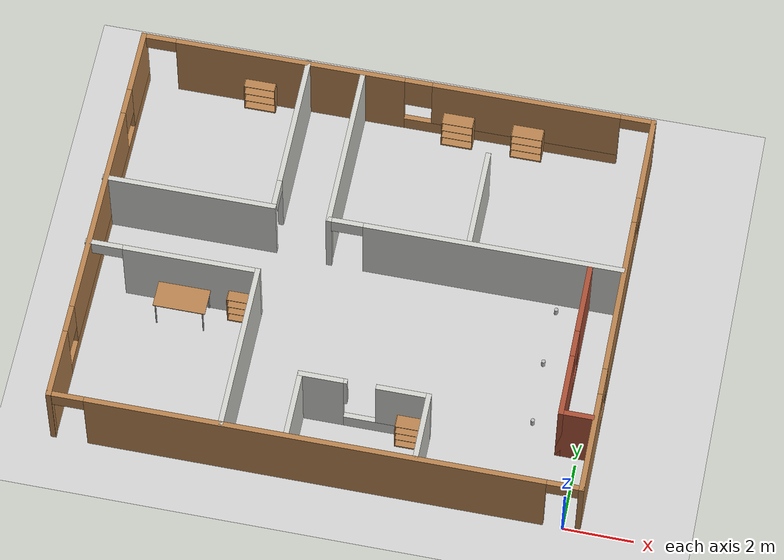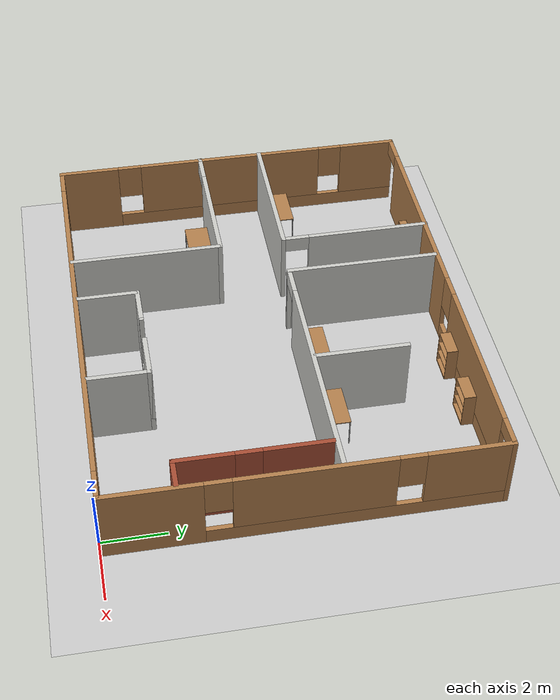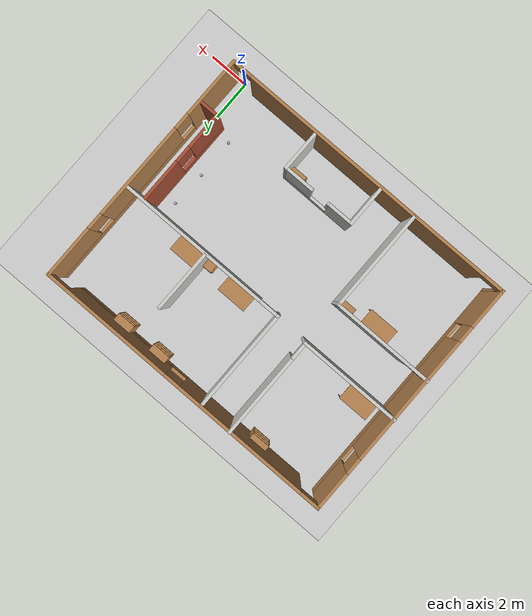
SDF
<sdf version="1.7">
 <world name="office.world">
  <light name="sun" type="directional">
   <pose>0 0 10 0 -0 0</pose>
   <diffuse>0.8 0.8 0.8 1</diffuse>
   <specular>0.2 0.2 0.2 1</specular>
   <attenuation>
    <range>1000</range>
    <constant>0.9</constant>
    <linear>0.01</linear>
    <quadratic>0.001</quadratic>
   </attenuation>
   <direction>-0.5 0.1 -0.9</direction>
   <spot><inner_angle>0</inner_angle><outer_angle>0</outer_angle><falloff>0</falloff></spot>
  </light>
  <model name="ground_plane">
   <static>1</static>
   <link name="link">
    <collision name="collision">
     <geometry><plane><normal>0 0 1</normal><size>100 100</size></plane></geometry>
     <surface><friction><ode><mu>100</mu><mu2>50</mu2></ode></friction></surface>
    </collision>
    <visual name="visual">
     <cast_shadows>0</cast_shadows>
     <geometry><plane><normal>0 0 1</normal><size>100 100</size></plane></geometry>
     <material>
      <script><uri>file://media/materials/scripts/gazebo.material</uri><name>Gazebo/Grey</name></script>
     </material>
    </visual>
   </link>
  </model>
  <gravity>0 0 -9.8</gravity>
  <magnetic_field>6e-06 2.3e-05 -4.2e-05</magnetic_field>
  <atmosphere type="adiabatic"/>
  <physics type="ode">
   <max_step_size>0.001</max_step_size>
   <real_time_factor>1</real_time_factor>
   <real_time_update_rate>1000</real_time_update_rate>
  </physics>
  <scene><ambient>0.4 0.4 0.4 1</ambient><background>0.7 0.7 0.7 1</background><shadows>1</shadows></scene>
  <audio><device>default</device></audio>
  <spherical_coordinates>
   <surface_model>EARTH_WGS84</surface_model>
   <latitude_deg>0</latitude_deg>
   <longitude_deg>0</longitude_deg>
   <elevation>0</elevation>
   <heading_deg>0</heading_deg>
  </spherical_coordinates>
  <model name="office">
   <pose>-6.85115 6.02821 0 0 -0 0</pose>
   <link name="Wall_18">
    <pose>-0.157794 -5.93469 0 0 -0 0</pose>
    <visual name="Wall_18_Visual_0">
     <pose>-7.42046 0 1.25 0 -0 0</pose>
     <geometry><box><size>0.159078 0.15 2.5</size></box></geometry>
     <material>
      <script><uri>file://media/materials/scripts/gazebo.material</uri><name>Gazebo/Wood</name></script>
      <ambient>1 1 1 1</ambient>
     </material>
     <meta><layer>0</layer></meta>
    </visual>
    <collision name="Wall_18_Collision_0">
     <geometry><box><size>0.159078 0.15 2.5</size></box></geometry>
     <pose>-7.42046 0 1.25 0 -0 0</pose>
    </collision>
    <visual name="Wall_18_Visual_1">
     <pose>0.007174 0 1.25 0 -0 0</pose>
     <geometry><box><size>12.8962 0.15 2.5</size></box></geometry>
     <material>
      <script><uri>file://media/materials/scripts/gazebo.material</uri><name>Gazebo/Wood</name></script>
      <ambient>1 1 1 1</ambient>
     </material>
     <meta><layer>0</layer></meta>
    </visual>
    <collision name="Wall_18_Collision_1">
     <geometry><box><size>12.8962 0.15 2.5</size></box></geometry>
     <pose>0.007174 0 1.25 0 -0 0</pose>
    </collision>
    <visual name="Wall_18_Visual_2">
     <pose>7.42764 0 1.25 0 -0 0</pose>
     <geometry><box><size>0.144729 0.15 2.5</size></box></geometry>
     <material>
      <script><uri>file://media/materials/scripts/gazebo.material</uri><name>Gazebo/Wood</name></script>
      <ambient>1 1 1 1</ambient>
     </material>
     <meta><layer>0</layer></meta>
    </visual>
    <collision name="Wall_18_Collision_2">
     <geometry><box><size>0.144729 0.15 2.5</size></box></geometry>
     <pose>7.42764 0 1.25 0 -0 0</pose>
    </collision>
    <visual name="Wall_18_Visual_3">
     <pose>-6.89092 0 2.25 0 -0 0</pose>
     <geometry><box><size>0.9 0.15 0.5</size></box></geometry>
     <material>
      <script><uri>file://media/materials/scripts/gazebo.material</uri><name>Gazebo/Wood</name></script>
      <ambient>1 1 1 1</ambient>
     </material>
     <meta><layer>0</layer></meta>
    </visual>
    <collision name="Wall_18_Collision_3">
     <geometry><box><size>0.9 0.15 0.5</size></box></geometry>
     <pose>-6.89092 0 2.25 0 -0 0</pose>
    </collision>
    <visual name="Wall_18_Visual_4">
     <pose>6.90527 0 2.25 0 -0 0</pose>
     <geometry><box><size>0.9 0.15 0.5</size></box></geometry>
     <material>
      <script><uri>file://media/materials/scripts/gazebo.material</uri><name>Gazebo/Wood</name></script>
      <ambient>1 1 1 1</ambient>
     </material>
     <meta><layer>0</layer></meta>
    </visual>
    <collision name="Wall_18_Collision_4">
     <geometry><box><size>0.9 0.15 0.5</size></box></geometry>
     <pose>6.90527 0 2.25 0 -0 0</pose>
    </collision>
   </link>
   <link name="Wall_20">
    <pose>7.26721 -0.009693 0 0 -0 1.5708</pose>
    <visual name="Wall_20_Visual_0">
     <pose>-4.48837 0 1.25 0 -0 0</pose>
     <geometry><box><size>3.02326 0.15 2.5</size></box></geometry>
     <material>
      <script><uri>file://media/materials/scripts/gazebo.material</uri><name>Gazebo/Wood</name></script>
      <ambient>1 1 1 1</ambient>
     </material>
     <meta><layer>0</layer></meta>
    </visual>
    <collision name="Wall_20_Collision_0">
     <geometry><box><size>3.02326 0.15 2.5</size></box></geometry>
     <pose>-4.48837 0 1.25 0 -0 0</pose>
    </collision>
    <visual name="Wall_20_Visual_1">
     <pose>1.51163 0 0.25 0 -0 0</pose>
     <geometry><box><size>8.97674 0.15 0.5</size></box></geometry>
     <material>
      <script><uri>file://media/materials/scripts/gazebo.material</uri><name>Gazebo/Wood</name></script>
      <ambient>1 1 1 1</ambient>
     </material>
     <meta><layer>0</layer></meta>
    </visual>
    <collision name="Wall_20_Collision_1">
     <geometry><box><size>8.97674 0.15 0.5</size></box></geometry>
     <pose>1.51163 0 0.25 0 -0 0</pose>
    </collision>
    <visual name="Wall_20_Visual_2">
     <pose>0.202385 0 1.5 0 -0 0</pose>
     <geometry><box><size>4.75824 0.15 2</size></box></geometry>
     <material>
      <script><uri>file://media/materials/scripts/gazebo.material</uri><name>Gazebo/Wood</name></script>
      <ambient>1 1 1 1</ambient>
     </material>
     <meta><layer>0</layer></meta>
    </visual>
    <collision name="Wall_20_Collision_2">
     <geometry><box><size>4.75824 0.15 2</size></box></geometry>
     <pose>0.202385 0 1.5 0 -0 0</pose>
    </collision>
    <visual name="Wall_20_Visual_3">
     <pose>4.69075 0 1.5 0 -0 0</pose>
     <geometry><box><size>2.61849 0.15 2</size></box></geometry>
     <material>
      <script><uri>file://media/materials/scripts/gazebo.material</uri><name>Gazebo/Wood</name></script>
      <ambient>1 1 1 1</ambient>
     </material>
     <meta><layer>0</layer></meta>
    </visual>
    <collision name="Wall_20_Collision_3">
     <geometry><box><size>2.61849 0.15 2</size></box></geometry>
     <pose>4.69075 0 1.5 0 -0 0</pose>
    </collision>
    <visual name="Wall_20_Visual_4">
     <pose>-2.57674 0 1.9 0 -0 0</pose>
     <geometry><box><size>0.8 0.15 1.2</size></box></geometry>
     <material>
      <script><uri>file://media/materials/scripts/gazebo.material</uri><name>Gazebo/Wood</name></script>
      <ambient>1 1 1 1</ambient>
     </material>
     <meta><layer>0</layer></meta>
    </visual>
    <collision name="Wall_20_Collision_4">
     <geometry><box><size>0.8 0.15 1.2</size></box></geometry>
     <pose>-2.57674 0 1.9 0 -0 0</pose>
    </collision>
    <visual name="Wall_20_Visual_5">
     <pose>2.98151 0 1.9 0 -0 0</pose>
     <geometry><box><size>0.8 0.15 1.2</size></box></geometry>
     <material>
      <script><uri>file://media/materials/scripts/gazebo.material</uri><name>Gazebo/Wood</name></script>
      <ambient>1 1 1 1</ambient>
     </material>
     <meta><layer>0</layer></meta>
    </visual>
    <collision name="Wall_20_Collision_5">
     <geometry><box><size>0.8 0.15 1.2</size></box></geometry>
     <pose>2.98151 0 1.9 0 -0 0</pose>
    </collision>
   </link>
   <link name="Wall_22">
    <pose>-7.58279 -0.009693 0 0 -0 1.5708</pose>
    <visual name="Wall_22_Visual_0">
     <pose>-4.97539 0 1.25 0 -0 0</pose>
     <geometry><box><size>2.04922 0.15 2.5</size></box></geometry>
     <material>
      <script><uri>file://media/materials/scripts/gazebo.material</uri><name>Gazebo/Wood</name></script>
      <ambient>1 1 1 1</ambient>
     </material>
     <meta><layer>0</layer></meta>
    </visual>
    <collision name="Wall_22_Collision_0">
     <geometry><box><size>2.04922 0.15 2.5</size></box></geometry>
     <pose>-4.97539 0 1.25 0 -0 0</pose>
    </collision>
    <visual name="Wall_22_Visual_1">
     <pose>1.02461 0 0.25 0 -0 0</pose>
     <geometry><box><size>9.95078 0.15 0.5</size></box></geometry>
     <material>
      <script><uri>file://media/materials/scripts/gazebo.material</uri><name>Gazebo/Wood</name></script>
      <ambient>1 1 1 1</ambient>
     </material>
     <meta><layer>0</layer></meta>
    </visual>
    <collision name="Wall_22_Collision_1">
     <geometry><box><size>9.95078 0.15 0.5</size></box></geometry>
     <pose>1.02461 0 0.25 0 -0 0</pose>
    </collision>
    <visual name="Wall_22_Visual_2">
     <pose>0.053552 0 1.5 0 -0 0</pose>
     <geometry><box><size>6.40865 0.15 2</size></box></geometry>
     <material>
      <script><uri>file://media/materials/scripts/gazebo.material</uri><name>Gazebo/Wood</name></script>
      <ambient>1 1 1 1</ambient>
     </material>
     <meta><layer>0</layer></meta>
    </visual>
    <collision name="Wall_22_Collision_2">
     <geometry><box><size>6.40865 0.15 2</size></box></geometry>
     <pose>0.053552 0 1.5 0 -0 0</pose>
    </collision>
    <visual name="Wall_22_Visual_3">
     <pose>5.02894 0 1.5 0 -0 0</pose>
     <geometry><box><size>1.94212 0.15 2</size></box></geometry>
     <material>
      <script><uri>file://media/materials/scripts/gazebo.material</uri><name>Gazebo/Wood</name></script>
      <ambient>1 1 1 1</ambient>
     </material>
     <meta><layer>0</layer></meta>
    </visual>
    <collision name="Wall_22_Collision_3">
     <geometry><box><size>1.94212 0.15 2</size></box></geometry>
     <pose>5.02894 0 1.5 0 -0 0</pose>
    </collision>
    <visual name="Wall_22_Visual_4">
     <pose>-3.55077 0 1.9 0 -0 0</pose>
     <geometry><box><size>0.8 0.15 1.2</size></box></geometry>
     <material>
      <script><uri>file://media/materials/scripts/gazebo.material</uri><name>Gazebo/Wood</name></script>
      <ambient>1 1 1 1</ambient>
     </material>
     <meta><layer>0</layer></meta>
    </visual>
    <collision name="Wall_22_Collision_4">
     <geometry><box><size>0.8 0.15 1.2</size></box></geometry>
     <pose>-3.55077 0 1.9 0 -0 0</pose>
    </collision>
    <visual name="Wall_22_Visual_5">
     <pose>3.65788 0 1.9 0 -0 0</pose>
     <geometry><box><size>0.8 0.15 1.2</size></box></geometry>
     <material>
      <script><uri>file://media/materials/scripts/gazebo.material</uri><name>Gazebo/Wood</name></script>
      <ambient>1 1 1 1</ambient>
     </material>
     <meta><layer>0</layer></meta>
    </visual>
    <collision name="Wall_22_Collision_5">
     <geometry><box><size>0.8 0.15 1.2</size></box></geometry>
     <pose>3.65788 0 1.9 0 -0 0</pose>
    </collision>
   </link>
   <link name="Wall_24">
    <pose>-0.157794 5.91531 0 0 -0 0</pose>
    <visual name="Wall_24_Visual_0">
     <pose>-7.43614 0 1.25 0 -0 0</pose>
     <geometry><box><size>0.127718 0.15 2.5</size></box></geometry>
     <material>
      <script><uri>file://media/materials/scripts/gazebo.material</uri><name>Gazebo/Wood</name></script>
      <ambient>1 1 1 1</ambient>
     </material>
     <meta><layer>0</layer></meta>
    </visual>
    <collision name="Wall_24_Collision_0">
     <geometry><box><size>0.127718 0.15 2.5</size></box></geometry>
     <pose>-7.43614 0 1.25 0 -0 0</pose>
    </collision>
    <visual name="Wall_24_Visual_1">
     <pose>-3.12232 0 1.25 0 -0 0</pose>
     <geometry><box><size>6.69992 0.15 2.5</size></box></geometry>
     <material>
      <script><uri>file://media/materials/scripts/gazebo.material</uri><name>Gazebo/Wood</name></script>
      <ambient>1 1 1 1</ambient>
     </material>
     <meta><layer>0</layer></meta>
    </visual>
    <collision name="Wall_24_Collision_1">
     <geometry><box><size>6.69992 0.15 2.5</size></box></geometry>
     <pose>-3.12232 0 1.25 0 -0 0</pose>
    </collision>
    <visual name="Wall_24_Visual_2">
     <pose>7.43563 0 1.25 0 -0 0</pose>
     <geometry><box><size>0.128742 0.15 2.5</size></box></geometry>
     <material>
      <script><uri>file://media/materials/scripts/gazebo.material</uri><name>Gazebo/Wood</name></script>
      <ambient>1 1 1 1</ambient>
     </material>
     <meta><layer>0</layer></meta>
    </visual>
    <collision name="Wall_24_Collision_2">
     <geometry><box><size>0.128742 0.15 2.5</size></box></geometry>
     <pose>7.43563 0 1.25 0 -0 0</pose>
    </collision>
    <visual name="Wall_24_Visual_3">
     <pose>3.34945 0 0.25 0 -0 0</pose>
     <geometry><box><size>6.24362 0.15 0.5</size></box></geometry>
     <material>
      <script><uri>file://media/materials/scripts/gazebo.material</uri><name>Gazebo/Wood</name></script>
      <ambient>1 1 1 1</ambient>
     </material>
     <meta><layer>0</layer></meta>
    </visual>
    <collision name="Wall_24_Collision_3">
     <geometry><box><size>6.24362 0.15 0.5</size></box></geometry>
     <pose>3.34945 0 0.25 0 -0 0</pose>
    </collision>
    <visual name="Wall_24_Visual_4">
     <pose>3.74945 0 1.5 0 -0 0</pose>
     <geometry><box><size>5.44362 0.15 2</size></box></geometry>
     <material>
      <script><uri>file://media/materials/scripts/gazebo.material</uri><name>Gazebo/Wood</name></script>
      <ambient>1 1 1 1</ambient>
     </material>
     <meta><layer>0</layer></meta>
    </visual>
    <collision name="Wall_24_Collision_4">
     <geometry><box><size>5.44362 0.15 2</size></box></geometry>
     <pose>3.74945 0 1.5 0 -0 0</pose>
    </collision>
    <visual name="Wall_24_Visual_5">
     <pose>0.62764 0 1.9 0 -0 0</pose>
     <geometry><box><size>0.8 0.15 1.2</size></box></geometry>
     <material>
      <script><uri>file://media/materials/scripts/gazebo.material</uri><name>Gazebo/Wood</name></script>
      <ambient>1 1 1 1</ambient>
     </material>
     <meta><layer>0</layer></meta>
    </visual>
    <collision name="Wall_24_Collision_5">
     <geometry><box><size>0.8 0.15 1.2</size></box></geometry>
     <pose>0.62764 0 1.9 0 -0 0</pose>
    </collision>
    <visual name="Wall_24_Visual_6">
     <pose>-6.92228 0 2.25 0 -0 0</pose>
     <geometry><box><size>0.9 0.15 0.5</size></box></geometry>
     <material>
      <script><uri>file://media/materials/scripts/gazebo.material</uri><name>Gazebo/Wood</name></script>
      <ambient>1 1 1 1</ambient>
     </material>
     <meta><layer>0</layer></meta>
    </visual>
    <collision name="Wall_24_Collision_6">
     <geometry><box><size>0.9 0.15 0.5</size></box></geometry>
     <pose>-6.92228 0 2.25 0 -0 0</pose>
    </collision>
    <visual name="Wall_24_Visual_7">
     <pose>6.92126 0 2.25 0 -0 0</pose>
     <geometry><box><size>0.9 0.15 0.5</size></box></geometry>
     <material>
      <script><uri>file://media/materials/scripts/gazebo.material</uri><name>Gazebo/Wood</name></script>
      <ambient>1 1 1 1</ambient>
     </material>
     <meta><layer>0</layer></meta>
    </visual>
    <collision name="Wall_24_Collision_7">
     <geometry><box><size>0.9 0.15 0.5</size></box></geometry>
     <pose>6.92126 0 2.25 0 -0 0</pose>
    </collision>
   </link>
   <link name="Wall_26">
    <collision name="Wall_26_Collision">
     <geometry><box><size>5 0.15 2.5</size></box></geometry>
     <pose>0 0 1.25 0 -0 0</pose>
    </collision>
    <visual name="Wall_26_Visual">
     <pose>0 0 1.25 0 -0 0</pose>
     <geometry><box><size>5 0.15 2.5</size></box></geometry>
     <material>
      <script><uri>file://media/materials/scripts/gazebo.material</uri><name>Gazebo/CeilingTiled</name></script>
      <ambient>1 1 1 1</ambient>
     </material>
     <meta><layer>0</layer></meta>
    </visual>
    <pose>-2.76199 -3.46401 0 0 -0 1.5708</pose>
   </link>
   <link name="Wall_28">
    <pose>-5.18699 -1.03901 0 0 -0 3.14159</pose>
    <visual name="Wall_28_Visual_0">
     <pose>-0.53426 0 1.25 0 -0 0</pose>
     <geometry><box><size>3.93148 0.15 2.5</size></box></geometry>
     <material>
      <script><uri>file://media/materials/scripts/gazebo.material</uri><name>Gazebo/CeilingTiled</name></script>
      <ambient>1 1 1 1</ambient>
     </material>
     <meta><layer>0</layer></meta>
    </visual>
    <collision name="Wall_28_Collision_0">
     <geometry><box><size>3.93148 0.15 2.5</size></box></geometry>
     <pose>-0.53426 0 1.25 0 -0 0</pose>
    </collision>
    <visual name="Wall_28_Visual_1">
     <pose>2.41574 0 1.25 0 -0 0</pose>
     <geometry><box><size>0.16852 0.15 2.5</size></box></geometry>
     <material>
      <script><uri>file://media/materials/scripts/gazebo.material</uri><name>Gazebo/CeilingTiled</name></script>
      <ambient>1 1 1 1</ambient>
     </material>
     <meta><layer>0</layer></meta>
    </visual>
    <collision name="Wall_28_Collision_1">
     <geometry><box><size>0.16852 0.15 2.5</size></box></geometry>
     <pose>2.41574 0 1.25 0 -0 0</pose>
    </collision>
    <visual name="Wall_28_Visual_2">
     <pose>1.88148 0 2.25 0 -0 0</pose>
     <geometry><box><size>0.9 0.15 0.5</size></box></geometry>
     <material>
      <script><uri>file://media/materials/scripts/gazebo.material</uri><name>Gazebo/CeilingTiled</name></script>
      <ambient>1 1 1 1</ambient>
     </material>
     <meta><layer>0</layer></meta>
    </visual>
    <collision name="Wall_28_Collision_2">
     <geometry><box><size>0.9 0.15 0.5</size></box></geometry>
     <pose>1.88148 0 2.25 0 -0 0</pose>
    </collision>
   </link>
   <link name="Wall_32">
    <pose>-2.75901 3.50969 0 0 -0 -1.5708</pose>
    <visual name="Wall_32_Visual_0">
     <pose>-0.46634 0 1.25 0 -0 0</pose>
     <geometry><box><size>4.06732 0.15 2.5</size></box></geometry>
     <material>
      <script><uri>file://media/materials/scripts/gazebo.material</uri><name>Gazebo/CeilingTiled</name></script>
      <ambient>1 1 1 1</ambient>
     </material>
     <meta><layer>0</layer></meta>
    </visual>
    <collision name="Wall_32_Collision_0">
     <geometry><box><size>4.06732 0.15 2.5</size></box></geometry>
     <pose>-0.46634 0 1.25 0 -0 0</pose>
    </collision>
    <visual name="Wall_32_Visual_1">
     <pose>2.48366 0 1.25 0 -0 0</pose>
     <geometry><box><size>0.032681 0.15 2.5</size></box></geometry>
     <material>
      <script><uri>file://media/materials/scripts/gazebo.material</uri><name>Gazebo/CeilingTiled</name></script>
      <ambient>1 1 1 1</ambient>
     </material>
     <meta><layer>0</layer></meta>
    </visual>
    <collision name="Wall_32_Collision_1">
     <geometry><box><size>0.032681 0.15 2.5</size></box></geometry>
     <pose>2.48366 0 1.25 0 -0 0</pose>
    </collision>
    <visual name="Wall_32_Visual_2">
     <pose>2.01732 0 2.25 0 -0 0</pose>
     <geometry><box><size>0.9 0.15 0.5</size></box></geometry>
     <material>
      <script><uri>file://media/materials/scripts/gazebo.material</uri><name>Gazebo/CeilingTiled</name></script>
      <ambient>1 1 1 1</ambient>
     </material>
     <meta><layer>0</layer></meta>
    </visual>
    <collision name="Wall_32_Collision_2">
     <geometry><box><size>0.9 0.15 0.5</size></box></geometry>
     <pose>2.01732 0 2.25 0 -0 0</pose>
    </collision>
   </link>
   <link name="Wall_34">
    <collision name="Wall_34_Collision">
     <geometry><box><size>5 0.15 2.5</size></box></geometry>
     <pose>0 0 1.25 0 -0 0</pose>
    </collision>
    <visual name="Wall_34_Visual">
     <pose>0 0 1.25 0 -0 0</pose>
     <geometry><box><size>5 0.15 2.5</size></box></geometry>
     <material>
      <script><uri>file://media/materials/scripts/gazebo.material</uri><name>Gazebo/CeilingTiled</name></script>
      <ambient>1 1 1 1</ambient>
     </material>
     <meta><layer>0</layer></meta>
    </visual>
    <pose>-5.18401 1.08469 0 0 -0 3.14159</pose>
   </link>
   <link name="Wall_36">
    <collision name="Wall_36_Collision">
     <geometry><box><size>5 0.15 2.5</size></box></geometry>
     <pose>0 0 1.25 0 -0 0</pose>
    </collision>
    <visual name="Wall_36_Visual">
     <pose>0 0 1.25 0 -0 0</pose>
     <geometry><box><size>5 0.15 2.5</size></box></geometry>
     <material>
      <script><uri>file://media/materials/scripts/gazebo.material</uri><name>Gazebo/CeilingTiled</name></script>
      <ambient>1 1 1 1</ambient>
     </material>
     <meta><layer>0</layer></meta>
    </visual>
    <pose>-1.15206 3.40845 0 0 -0 -1.5708</pose>
   </link>
   <link name="Wall_38">
    <pose>3.02294 0.98345 0 0 -0 0</pose>
    <visual name="Wall_38_Visual_0">
     <pose>-4.16728 0 1.25 0 -0 0</pose>
     <geometry><box><size>0.165448 0.15 2.5</size></box></geometry>
     <material>
      <script><uri>file://media/materials/scripts/gazebo.material</uri><name>Gazebo/CeilingTiled</name></script>
      <ambient>1 1 1 1</ambient>
     </material>
     <meta><layer>0</layer></meta>
    </visual>
    <collision name="Wall_38_Collision_0">
     <geometry><box><size>0.165448 0.15 2.5</size></box></geometry>
     <pose>-4.16728 0 1.25 0 -0 0</pose>
    </collision>
    <visual name="Wall_38_Visual_1">
     <pose>0.532724 0 1.25 0 -0 0</pose>
     <geometry><box><size>7.43455 0.15 2.5</size></box></geometry>
     <material>
      <script><uri>file://media/materials/scripts/gazebo.material</uri><name>Gazebo/CeilingTiled</name></script>
      <ambient>1 1 1 1</ambient>
     </material>
     <meta><layer>0</layer></meta>
    </visual>
    <collision name="Wall_38_Collision_1">
     <geometry><box><size>7.43455 0.15 2.5</size></box></geometry>
     <pose>0.532724 0 1.25 0 -0 0</pose>
    </collision>
    <visual name="Wall_38_Visual_2">
     <pose>-3.63455 0 2.25 0 -0 0</pose>
     <geometry><box><size>0.9 0.15 0.5</size></box></geometry>
     <material>
      <script><uri>file://media/materials/scripts/gazebo.material</uri><name>Gazebo/CeilingTiled</name></script>
      <ambient>1 1 1 1</ambient>
     </material>
     <meta><layer>0</layer></meta>
    </visual>
    <collision name="Wall_38_Collision_2">
     <geometry><box><size>0.9 0.15 0.5</size></box></geometry>
     <pose>-3.63455 0 2.25 0 -0 0</pose>
    </collision>
   </link>
   <link name="Wall_40">
    <collision name="Wall_40_Collision">
     <geometry><box><size>3 0.15 2.5</size></box></geometry>
     <pose>0 0 1.25 0 -0 0</pose>
    </collision>
    <visual name="Wall_40_Visual">
     <pose>0 0 1.25 0 -0 0</pose>
     <geometry><box><size>3 0.15 2.5</size></box></geometry>
     <material>
      <script><uri>file://media/materials/scripts/gazebo.material</uri><name>Gazebo/CeilingTiled</name></script>
      <ambient>1 1 1 1</ambient>
     </material>
     <meta><layer>0</layer></meta>
    </visual>
    <pose>2.85102 2.49115 0 0 -0 1.5708</pose>
   </link>
   <link name="Wall_44">
    <collision name="Wall_44_Collision">
     <geometry><box><size>2 0.15 2.5</size></box></geometry>
     <pose>0 0 1.25 0 -0 0</pose>
    </collision>
    <visual name="Wall_44_Visual">
     <pose>0 0 1.25 0 -0 0</pose>
     <geometry><box><size>2 0.15 2.5</size></box></geometry>
     <material>
      <script><uri>file://media/materials/scripts/gazebo.material</uri><name>Gazebo/CeilingTiled</name></script>
      <ambient>1 1 1 1</ambient>
     </material>
     <meta><layer>0</layer></meta>
    </visual>
    <pose>-0.937305 -4.89788 0 0 -0 1.5708</pose>
   </link>
   <link name="Wall_45">
    <pose>0.862695 -3.97288 0 0 -0 0</pose>
    <visual name="Wall_45_Visual_0">
     <pose>-1.22839 0 1.25 0 -0 0</pose>
     <geometry><box><size>1.29322 0.15 2.5</size></box></geometry>
     <material>
      <script><uri>file://media/materials/scripts/gazebo.material</uri><name>Gazebo/CeilingTiled</name></script>
      <ambient>1 1 1 1</ambient>
     </material>
     <meta><layer>0</layer></meta>
    </visual>
    <collision name="Wall_45_Collision_0">
     <geometry><box><size>1.29322 0.15 2.5</size></box></geometry>
     <pose>-1.22839 0 1.25 0 -0 0</pose>
    </collision>
    <visual name="Wall_45_Visual_1">
     <pose>0.646612 0 0.25 0 -0 0</pose>
     <geometry><box><size>2.45678 0.15 0.5</size></box></geometry>
     <material>
      <script><uri>file://media/materials/scripts/gazebo.material</uri><name>Gazebo/CeilingTiled</name></script>
      <ambient>1 1 1 1</ambient>
     </material>
     <meta><layer>0</layer></meta>
    </visual>
    <collision name="Wall_45_Collision_1">
     <geometry><box><size>2.45678 0.15 0.5</size></box></geometry>
     <pose>0.646612 0 0.25 0 -0 0</pose>
    </collision>
    <visual name="Wall_45_Visual_2">
     <pose>1.09938 0 1.5 0 -0 0</pose>
     <geometry><box><size>1.55124 0.15 2</size></box></geometry>
     <material>
      <script><uri>file://media/materials/scripts/gazebo.material</uri><name>Gazebo/CeilingTiled</name></script>
      <ambient>1 1 1 1</ambient>
     </material>
     <meta><layer>0</layer></meta>
    </visual>
    <collision name="Wall_45_Collision_2">
     <geometry><box><size>1.55124 0.15 2</size></box></geometry>
     <pose>1.09938 0 1.5 0 -0 0</pose>
    </collision>
    <visual name="Wall_45_Visual_3">
     <pose>-0.529009 0 1.9 0 -0 0</pose>
     <geometry><box><size>0.105536 0.15 1.2</size></box></geometry>
     <material>
      <script><uri>file://media/materials/scripts/gazebo.material</uri><name>Gazebo/CeilingTiled</name></script>
      <ambient>1 1 1 1</ambient>
     </material>
     <meta><layer>0</layer></meta>
    </visual>
    <collision name="Wall_45_Collision_3">
     <geometry><box><size>0.105536 0.15 1.2</size></box></geometry>
     <pose>-0.529009 0 1.9 0 -0 0</pose>
    </collision>
   </link>
   <link name="Wall_46">
    <collision name="Wall_46_Collision">
     <geometry><box><size>2 0.15 2.5</size></box></geometry>
     <pose>0 0 1.25 0 -0 0</pose>
    </collision>
    <visual name="Wall_46_Visual">
     <pose>0 0 1.25 0 -0 0</pose>
     <geometry><box><size>2 0.15 2.5</size></box></geometry>
     <material>
      <script><uri>file://media/materials/scripts/gazebo.material</uri><name>Gazebo/CeilingTiled</name></script>
      <ambient>1 1 1 1</ambient>
     </material>
     <meta><layer>0</layer></meta>
    </visual>
    <pose>2.66269 -4.89788 0 0 -0 -1.5708</pose>
   </link>
   <link name="Wall_48">
    <pose>6.30952 -1.43891 0 0 -0 -1.5708</pose>
    <visual name="Wall_48_Visual_0">
     <pose>-1.32383 0 1.25 0 -0 0</pose>
     <geometry><box><size>2.10234 0.15 2.5</size></box></geometry>
     <material>
      <script><uri>file://media/materials/scripts/gazebo.material</uri><name>Gazebo/Bricks</name></script>
      <ambient>1 1 1 1</ambient>
     </material>
     <meta><layer>0</layer></meta>
    </visual>
    <collision name="Wall_48_Collision_0">
     <geometry><box><size>2.10234 0.15 2.5</size></box></geometry>
     <pose>-1.32383 0 1.25 0 -0 0</pose>
    </collision>
    <visual name="Wall_48_Visual_1">
     <pose>1.05117 0 0.25 0 -0 0</pose>
     <geometry><box><size>2.64766 0.15 0.5</size></box></geometry>
     <material>
      <script><uri>file://media/materials/scripts/gazebo.material</uri><name>Gazebo/Bricks</name></script>
      <ambient>1 1 1 1</ambient>
     </material>
     <meta><layer>0</layer></meta>
    </visual>
    <collision name="Wall_48_Collision_1">
     <geometry><box><size>2.64766 0.15 0.5</size></box></geometry>
     <pose>1.05117 0 0.25 0 -0 0</pose>
    </collision>
    <visual name="Wall_48_Visual_2">
     <pose>1.45117 0 1.5 0 -0 0</pose>
     <geometry><box><size>1.84766 0.15 2</size></box></geometry>
     <material>
      <script><uri>file://media/materials/scripts/gazebo.material</uri><name>Gazebo/Bricks</name></script>
      <ambient>1 1 1 1</ambient>
     </material>
     <meta><layer>0</layer></meta>
    </visual>
    <collision name="Wall_48_Collision_2">
     <geometry><box><size>1.84766 0.15 2</size></box></geometry>
     <pose>1.45117 0 1.5 0 -0 0</pose>
    </collision>
    <visual name="Wall_48_Visual_3">
     <pose>0.127335 0 1.9 0 -0 0</pose>
     <geometry><box><size>0.8 0.15 1.2</size></box></geometry>
     <material>
      <script><uri>file://media/materials/scripts/gazebo.material</uri><name>Gazebo/Bricks</name></script>
      <ambient>1 1 1 1</ambient>
     </material>
     <meta><layer>0</layer></meta>
    </visual>
    <collision name="Wall_48_Collision_3">
     <geometry><box><size>0.8 0.15 1.2</size></box></geometry>
     <pose>0.127335 0 1.9 0 -0 0</pose>
    </collision>
   </link>
   <link name="Wall_49">
    <collision name="Wall_49_Collision">
     <geometry><box><size>1 0.15 2.5</size></box></geometry>
     <pose>0 0 1.25 0 -0 0</pose>
    </collision>
    <visual name="Wall_49_Visual">
     <pose>0 0 1.25 0 -0 0</pose>
     <geometry><box><size>1 0.15 2.5</size></box></geometry>
     <material>
      <script><uri>file://media/materials/scripts/gazebo.material</uri><name>Gazebo/Bricks</name></script>
      <ambient>1 1 1 1</ambient>
     </material>
     <meta><layer>0</layer></meta>
    </visual>
    <pose>6.73452 -3.73891 0 0 -0 0</pose>
   </link>
   <static>1</static>
  </model>
  <light name="user_point_light_0" type="point">
   <pose>-13.0253 3.22878 1 0 -0 0</pose>
   <diffuse>0.5 0.5 0.5 1</diffuse>
   <specular>0.1 0.1 0.1 1</specular>
   <attenuation>
    <range>20</range>
    <constant>0.5</constant>
    <linear>0.01</linear>
    <quadratic>0.001</quadratic>
   </attenuation>
   <cast_shadows>0</cast_shadows>
   <direction>0 0 -1</direction>
   <spot><inner_angle>0</inner_angle><outer_angle>0</outer_angle><falloff>0</falloff></spot>
  </light>
  <light name="user_point_light_1" type="point">
   <pose>-13.235 10.4296 1 0 -0 0</pose>
   <diffuse>0.5 0.5 0.5 1</diffuse>
   <specular>0.1 0.1 0.1 1</specular>
   <attenuation>
    <range>20</range>
    <constant>0.5</constant>
    <linear>0.01</linear>
    <quadratic>0.001</quadratic>
   </attenuation>
   <cast_shadows>0</cast_shadows>
   <direction>0 0 -1</direction>
   <spot><inner_angle>0</inner_angle><outer_angle>0</outer_angle><falloff>0</falloff></spot>
  </light>
  <light name="user_point_light_2" type="point">
   <pose>-7.09221 4.9466 1 0 -0 0</pose>
   <diffuse>0.5 0.5 0.5 1</diffuse>
   <specular>0.1 0.1 0.1 1</specular>
   <attenuation>
    <range>20</range>
    <constant>0.5</constant>
    <linear>0.01</linear>
    <quadratic>0.001</quadratic>
   </attenuation>
   <cast_shadows>0</cast_shadows>
   <direction>0 0 -1</direction>
   <spot><inner_angle>0</inner_angle><outer_angle>0</outer_angle><falloff>0</falloff></spot>
  </light>
  <light name="user_point_light_3" type="point">
   <pose>-3.34108 4.6762 1 0 -0 0</pose>
   <diffuse>0.5 0.5 0.5 1</diffuse>
   <specular>0.1 0.1 0.1 1</specular>
   <attenuation>
    <range>20</range>
    <constant>0.5</constant>
    <linear>0.01</linear>
    <quadratic>0.001</quadratic>
   </attenuation>
   <cast_shadows>0</cast_shadows>
   <direction>0 0 -1</direction>
   <spot><inner_angle>0</inner_angle><outer_angle>0</outer_angle><falloff>0</falloff></spot>
  </light>
  <light name="user_point_light_4" type="point">
   <pose>-6.70273 9.82594 1 0 -0 0</pose>
   <diffuse>0.5 0.5 0.5 1</diffuse>
   <specular>0.1 0.1 0.1 1</specular>
   <attenuation>
    <range>20</range>
    <constant>0.5</constant>
    <linear>0.01</linear>
    <quadratic>0.001</quadratic>
   </attenuation>
   <cast_shadows>0</cast_shadows>
   <direction>0 0 -1</direction>
   <spot><inner_angle>0</inner_angle><outer_angle>0</outer_angle><falloff>0</falloff></spot>
  </light>
  <light name="user_point_light_5" type="point">
   <pose>-1.76431 9.90114 1 0 -0 0</pose>
   <diffuse>0.5 0.5 0.5 1</diffuse>
   <specular>0.1 0.1 0.1 1</specular>
   <attenuation>
    <range>20</range>
    <constant>0.5</constant>
    <linear>0.01</linear>
    <quadratic>0.001</quadratic>
   </attenuation>
   <cast_shadows>0</cast_shadows>
   <direction>0 0 -1</direction>
   <spot><inner_angle>0</inner_angle><outer_angle>0</outer_angle><falloff>0</falloff></spot>
  </light>
  <light name="user_point_light_6" type="point">
   <pose>-6.82673 1.37504 1 0 -0 0</pose>
   <diffuse>0.5 0.5 0.5 1</diffuse>
   <specular>0.1 0.1 0.1 1</specular>
   <attenuation>
    <range>20</range>
    <constant>0.5</constant>
    <linear>0.01</linear>
    <quadratic>0.001</quadratic>
   </attenuation>
   <cast_shadows>0</cast_shadows>
   <direction>0 0 -1</direction>
   <spot><inner_angle>0</inner_angle><outer_angle>0</outer_angle><falloff>0</falloff></spot>
  </light>
  <light name="user_spot_light_0" type="spot">
   <pose>-0.02547 2.95856 1 0 -0 0</pose>
   <diffuse>0.5 0.5 0.5 1</diffuse>
   <specular>0.1 0.1 0.1 1</specular>
   <direction>0 0 -1</direction>
   <attenuation>
    <range>20</range>
    <constant>0.5</constant>
    <linear>0.01</linear>
    <quadratic>0.001</quadratic>
   </attenuation>
   <cast_shadows>0</cast_shadows>
   <spot><inner_angle>0.6</inner_angle><outer_angle>1</outer_angle><falloff>1</falloff></spot>
  </light>
  <light name="user_spot_light_1" type="spot">
   <pose>-0.058135 4.21215 1 0 -0 0</pose>
   <diffuse>0.5 0.5 0.5 1</diffuse>
   <specular>0.1 0.1 0.1 1</specular>
   <direction>0 0 -1</direction>
   <attenuation>
    <range>20</range>
    <constant>0.5</constant>
    <linear>0.01</linear>
    <quadratic>0.001</quadratic>
   </attenuation>
   <cast_shadows>0</cast_shadows>
   <spot><inner_angle>0.6</inner_angle><outer_angle>1</outer_angle><falloff>1</falloff></spot>
  </light>
  <light name="user_spot_light_2" type="spot">
   <pose>-0.020808 5.34888 1 0 -0 0</pose>
   <diffuse>0.5 0.5 0.5 1</diffuse>
   <specular>0.1 0.1 0.1 1</specular>
   <direction>0 0 -1</direction>
   <attenuation>
    <range>20</range>
    <constant>0.5</constant>
    <linear>0.01</linear>
    <quadratic>0.001</quadratic>
   </attenuation>
   <cast_shadows>0</cast_shadows>
   <spot><inner_angle>0.6</inner_angle><outer_angle>1</outer_angle><falloff>1</falloff></spot>
  </light>
  <light name="user_spot_light_3" type="spot">
   <pose>-0.072959 6.37848 1 0 -0 0</pose>
   <diffuse>0.5 0.5 0.5 1</diffuse>
   <specular>0.1 0.1 0.1 1</specular>
   <direction>0 0 -1</direction>
   <attenuation>
    <range>20</range>
    <constant>0.5</constant>
    <linear>0.01</linear>
    <quadratic>0.001</quadratic>
   </attenuation>
   <cast_shadows>0</cast_shadows>
   <spot><inner_angle>0.6</inner_angle><outer_angle>1</outer_angle><falloff>1</falloff></spot>
  </light>
  <model name="cabinet">
   <static>1</static>
   <link name="cabinet_bottom_plate">
    <inertial>
     <pose>0 0 -1 0 -0 0</pose>
     <inertia><ixx>2.05</ixx><ixy>0</ixy><ixz>0</ixz><iyy>2.05</iyy><iyz>0</iyz><izz>2.05</izz></inertia>
     <mass>25</mass>
    </inertial>
    <collision name="cabinet_bottom_plate_geom">
     <pose>0 0 0.01 0 -0 0</pose>
     <geometry><box><size>0.45 0.45 0.02</size></box></geometry>
    </collision>
    <visual name="cabinet_bottom_plate_geom_visual">
     <pose>0 0 0.01 0 -0 0</pose>
     <geometry><box><size>0.45 0.45 0.02</size></box></geometry>
     <material>
      <script><uri>file://media/materials/scripts/gazebo.material</uri><name>Gazebo/Wood</name></script>
     </material>
    </visual>
    <collision name="cabinet_bottom_plate_geom_cabinet_back_plate">
     <pose>0.235 0 0.51 0 -0 0</pose>
     <geometry><box><size>0.02 0.45 1.02</size></box></geometry>
    </collision>
    <visual name="cabinet_bottom_plate_geom_cabinet_back_plate_visual">
     <pose>0.235 0 0.51 0 -0 0</pose>
     <geometry><box><size>0.02 0.45 1.02</size></box></geometry>
     <material>
      <script><uri>file://media/materials/scripts/gazebo.material</uri><name>Gazebo/Wood</name></script>
     </material>
    </visual>
    <collision name="cabinet_bottom_plate_geom_cabinet_left_plate">
     <pose>0 0.235 0.51 0 -0 0</pose>
     <geometry><box><size>0.45 0.02 1.02</size></box></geometry>
    </collision>
    <visual name="cabinet_bottom_plate_geom_cabinet_left_plate_visual">
     <pose>0 0.235 0.51 0 -0 0</pose>
     <geometry><box><size>0.45 0.02 1.02</size></box></geometry>
     <material>
      <script><uri>file://media/materials/scripts/gazebo.material</uri><name>Gazebo/Wood</name></script>
     </material>
    </visual>
    <collision name="cabinet_bottom_plate_geom_cabinet_middle_plate">
     <pose>0 0 0.51 0 -0 0</pose>
     <geometry><box><size>0.45 0.45 0.02</size></box></geometry>
    </collision>
    <visual name="cabinet_bottom_plate_geom_cabinet_middle_plate_visual">
     <pose>0 0 0.51 0 -0 0</pose>
     <geometry><box><size>0.45 0.45 0.02</size></box></geometry>
     <material>
      <script><uri>file://media/materials/scripts/gazebo.material</uri><name>Gazebo/Wood</name></script>
     </material>
    </visual>
    <collision name="cabinet_bottom_plate_geom_cabinet_right_plate">
     <pose>0 -0.235 0.51 0 -0 0</pose>
     <geometry><box><size>0.45 0.02 1.02</size></box></geometry>
    </collision>
    <visual name="cabinet_bottom_plate_geom_cabinet_right_plate_visual">
     <pose>0 -0.235 0.51 0 -0 0</pose>
     <geometry><box><size>0.45 0.02 1.02</size></box></geometry>
     <material>
      <script><uri>file://media/materials/scripts/gazebo.material</uri><name>Gazebo/Wood</name></script>
     </material>
    </visual>
    <collision name="cabinet_bottom_plate_geom_cabinet_top_plate">
     <pose>0 0 1.01 0 -0 0</pose>
     <geometry><box><size>0.45 0.45 0.02</size></box></geometry>
    </collision>
    <visual name="cabinet_bottom_plate_geom_cabinet_top_plate_visual">
     <pose>0 0 1.01 0 -0 0</pose>
     <geometry><box><size>0.45 0.45 0.02</size></box></geometry>
     <material>
      <script><uri>file://media/materials/scripts/gazebo.material</uri><name>Gazebo/Wood</name></script>
     </material>
    </visual>
   </link>
   <pose>-4.3117 7.32168 0 0 -0 0</pose>
  </model>
  <model name="bookshelf">
   <static>1</static>
   <link name="link">
    <inertial><mass>1</mass></inertial>
    <collision name="back">
     <pose>0 0.005 0.6 0 -0 0</pose>
     <geometry><box><size>0.9 0.01 1.2</size></box></geometry>
    </collision>
    <visual name="visual1">
     <pose>0 0.005 0.6 0 -0 0</pose>
     <geometry><box><size>0.9 0.01 1.2</size></box></geometry>
     <material>
      <script><uri>file://media/materials/scripts/gazebo.material</uri><name>Gazebo/Wood</name></script>
     </material>
    </visual>
    <collision name="left_side">
     <pose>0.45 -0.195 0.6 0 -0 0</pose>
     <geometry><box><size>0.02 0.4 1.2</size></box></geometry>
    </collision>
    <visual name="visual2">
     <pose>0.45 -0.195 0.6 0 -0 0</pose>
     <geometry><box><size>0.02 0.4 1.2</size></box></geometry>
     <material>
      <script><uri>file://media/materials/scripts/gazebo.material</uri><name>Gazebo/Wood</name></script>
     </material>
    </visual>
    <collision name="right_side">
     <pose>-0.45 -0.195 0.6 0 -0 0</pose>
     <geometry><box><size>0.02 0.4 1.2</size></box></geometry>
    </collision>
    <visual name="visual3">
     <pose>-0.45 -0.195 0.6 0 -0 0</pose>
     <geometry><box><size>0.02 0.4 1.2</size></box></geometry>
     <material>
      <script><uri>file://media/materials/scripts/gazebo.material</uri><name>Gazebo/Wood</name></script>
     </material>
    </visual>
    <collision name="bottom">
     <pose>0 -0.195 0.03 0 -0 0</pose>
     <geometry><box><size>0.88 0.4 0.06</size></box></geometry>
    </collision>
    <visual name="visual4">
     <pose>0 -0.195 0.03 0 -0 0</pose>
     <geometry><box><size>0.88 0.4 0.06</size></box></geometry>
     <material>
      <script><uri>file://media/materials/scripts/gazebo.material</uri><name>Gazebo/Wood</name></script>
     </material>
    </visual>
    <collision name="top">
     <pose>0 -0.195 1.19 0 -0 0</pose>
     <geometry><box><size>0.88 0.4 0.02</size></box></geometry>
    </collision>
    <visual name="visual5">
     <pose>0 -0.195 1.19 0 -0 0</pose>
     <geometry><box><size>0.88 0.4 0.02</size></box></geometry>
     <material>
      <script><uri>file://media/materials/scripts/gazebo.material</uri><name>Gazebo/Wood</name></script>
     </material>
    </visual>
    <collision name="low_shelf">
     <pose>0 -0.195 0.43 0 -0 0</pose>
     <geometry><box><size>0.88 0.4 0.02</size></box></geometry>
    </collision>
    <visual name="visual6">
     <pose>0 -0.195 0.43 0 -0 0</pose>
     <geometry><box><size>0.88 0.4 0.02</size></box></geometry>
     <material>
      <script><uri>file://media/materials/scripts/gazebo.material</uri><name>Gazebo/Wood</name></script>
     </material>
    </visual>
    <collision name="high_shelf">
     <pose>0 -0.195 0.8 0 -0 0</pose>
     <geometry><box><size>0.88 0.4 0.02</size></box></geometry>
    </collision>
    <visual name="visual7">
     <pose>0 -0.195 0.8 0 -0 0</pose>
     <geometry><box><size>0.88 0.4 0.02</size></box></geometry>
     <material>
      <script><uri>file://media/materials/scripts/gazebo.material</uri><name>Gazebo/Wood</name></script>
     </material>
    </visual>
   </link>
   <pose>-5.16485 11.9017 0 0 -0 0</pose>
  </model>
  <model name="bookshelf_0">
   <static>1</static>
   <link name="link">
    <inertial><mass>1</mass></inertial>
    <collision name="back">
     <pose>0 0.005 0.6 0 -0 0</pose>
     <geometry><box><size>0.9 0.01 1.2</size></box></geometry>
    </collision>
    <visual name="visual1">
     <pose>0 0.005 0.6 0 -0 0</pose>
     <geometry><box><size>0.9 0.01 1.2</size></box></geometry>
     <material>
      <script><uri>file://media/materials/scripts/gazebo.material</uri><name>Gazebo/Wood</name></script>
     </material>
    </visual>
    <collision name="left_side">
     <pose>0.45 -0.195 0.6 0 -0 0</pose>
     <geometry><box><size>0.02 0.4 1.2</size></box></geometry>
    </collision>
    <visual name="visual2">
     <pose>0.45 -0.195 0.6 0 -0 0</pose>
     <geometry><box><size>0.02 0.4 1.2</size></box></geometry>
     <material>
      <script><uri>file://media/materials/scripts/gazebo.material</uri><name>Gazebo/Wood</name></script>
     </material>
    </visual>
    <collision name="right_side">
     <pose>-0.45 -0.195 0.6 0 -0 0</pose>
     <geometry><box><size>0.02 0.4 1.2</size></box></geometry>
    </collision>
    <visual name="visual3">
     <pose>-0.45 -0.195 0.6 0 -0 0</pose>
     <geometry><box><size>0.02 0.4 1.2</size></box></geometry>
     <material>
      <script><uri>file://media/materials/scripts/gazebo.material</uri><name>Gazebo/Wood</name></script>
     </material>
    </visual>
    <collision name="bottom">
     <pose>0 -0.195 0.03 0 -0 0</pose>
     <geometry><box><size>0.88 0.4 0.06</size></box></geometry>
    </collision>
    <visual name="visual4">
     <pose>0 -0.195 0.03 0 -0 0</pose>
     <geometry><box><size>0.88 0.4 0.06</size></box></geometry>
     <material>
      <script><uri>file://media/materials/scripts/gazebo.material</uri><name>Gazebo/Wood</name></script>
     </material>
    </visual>
    <collision name="top">
     <pose>0 -0.195 1.19 0 -0 0</pose>
     <geometry><box><size>0.88 0.4 0.02</size></box></geometry>
    </collision>
    <visual name="visual5">
     <pose>0 -0.195 1.19 0 -0 0</pose>
     <geometry><box><size>0.88 0.4 0.02</size></box></geometry>
     <material>
      <script><uri>file://media/materials/scripts/gazebo.material</uri><name>Gazebo/Wood</name></script>
     </material>
    </visual>
    <collision name="low_shelf">
     <pose>0 -0.195 0.43 0 -0 0</pose>
     <geometry><box><size>0.88 0.4 0.02</size></box></geometry>
    </collision>
    <visual name="visual6">
     <pose>0 -0.195 0.43 0 -0 0</pose>
     <geometry><box><size>0.88 0.4 0.02</size></box></geometry>
     <material>
      <script><uri>file://media/materials/scripts/gazebo.material</uri><name>Gazebo/Wood</name></script>
     </material>
    </visual>
    <collision name="high_shelf">
     <pose>0 -0.195 0.8 0 -0 0</pose>
     <geometry><box><size>0.88 0.4 0.02</size></box></geometry>
    </collision>
    <visual name="visual7">
     <pose>0 -0.195 0.8 0 -0 0</pose>
     <geometry><box><size>0.88 0.4 0.02</size></box></geometry>
     <material>
      <script><uri>file://media/materials/scripts/gazebo.material</uri><name>Gazebo/Wood</name></script>
     </material>
    </visual>
   </link>
   <pose>-3.12828 11.8826 0 0 -0 0</pose>
  </model>
  <model name="beer">
   <link name="link">
    <pose>0 0 0.115 0 -0 0</pose>
    <inertial>
     <mass>0.39</mass>
     <inertia><ixx>0.00058</ixx><ixy>0</ixy><ixz>0</ixz><iyy>0.00058</iyy><iyz>0</iyz><izz>0.00019</izz></inertia>
    </inertial>
    <collision name="collision">
     <geometry><cylinder><radius>0.055</radius><length>0.23</length></cylinder></geometry>
    </collision>
    <visual name="visual">
     <geometry><cylinder><radius>0.055</radius><length>0.23</length></cylinder></geometry>
     <material>
      <script>
       <uri>model://beer/materials/scripts</uri>
       <uri>model://beer/materials/textures</uri>
       <name>Beer/Diffuse</name>
      </script>
     </material>
    </visual>
   </link>
   <pose>-1.31931 6.23628 1.00499 -3.14158 -1.1e-05 -0.392211</pose>
  </model>
  <model name="beer_0">
   <link name="link">
    <pose>0 0 0.115 0 -0 0</pose>
    <inertial>
     <mass>0.39</mass>
     <inertia><ixx>0.00058</ixx><ixy>0</ixy><ixz>0</ixz><iyy>0.00058</iyy><iyz>0</iyz><izz>0.00019</izz></inertia>
    </inertial>
    <collision name="collision">
     <geometry><cylinder><radius>0.055</radius><length>0.23</length></cylinder></geometry>
    </collision>
    <visual name="visual">
     <geometry><cylinder><radius>0.055</radius><length>0.23</length></cylinder></geometry>
     <material>
      <script>
       <uri>model://beer/materials/scripts</uri>
       <uri>model://beer/materials/textures</uri>
       <name>Beer/Diffuse</name>
      </script>
     </material>
    </visual>
   </link>
   <pose>-1.38207 4.54183 1.005 3.14157 1e-05 -3.13102</pose>
  </model>
  <model name="beer_1">
   <link name="link">
    <pose>0 0 0.115 0 -0 0</pose>
    <inertial>
     <mass>0.39</mass>
     <inertia><ixx>0.00058</ixx><ixy>0</ixy><ixz>0</ixz><iyy>0.00058</iyy><iyz>0</iyz><izz>0.00019</izz></inertia>
    </inertial>
    <collision name="collision">
     <geometry><cylinder><radius>0.055</radius><length>0.23</length></cylinder></geometry>
    </collision>
    <visual name="visual">
     <geometry><cylinder><radius>0.055</radius><length>0.23</length></cylinder></geometry>
     <material>
      <script>
       <uri>model://beer/materials/scripts</uri>
       <uri>model://beer/materials/textures</uri>
       <name>Beer/Diffuse</name>
      </script>
     </material>
    </visual>
   </link>
   <pose>-1.34397 2.65667 1.00499 -3.14158 3.2e-05 -3.13092</pose>
  </model>
  <model name="bookshelf_1">
   <static>1</static>
   <link name="link">
    <inertial><mass>1</mass></inertial>
    <collision name="back">
     <pose>0 0.005 0.6 0 -0 0</pose>
     <geometry><box><size>0.9 0.01 1.2</size></box></geometry>
    </collision>
    <visual name="visual1">
     <pose>0 0.005 0.6 0 -0 0</pose>
     <geometry><box><size>0.9 0.01 1.2</size></box></geometry>
     <material>
      <script><uri>file://media/materials/scripts/gazebo.material</uri><name>Gazebo/Wood</name></script>
     </material>
    </visual>
    <collision name="left_side">
     <pose>0.45 -0.195 0.6 0 -0 0</pose>
     <geometry><box><size>0.02 0.4 1.2</size></box></geometry>
    </collision>
    <visual name="visual2">
     <pose>0.45 -0.195 0.6 0 -0 0</pose>
     <geometry><box><size>0.02 0.4 1.2</size></box></geometry>
     <material>
      <script><uri>file://media/materials/scripts/gazebo.material</uri><name>Gazebo/Wood</name></script>
     </material>
    </visual>
    <collision name="right_side">
     <pose>-0.45 -0.195 0.6 0 -0 0</pose>
     <geometry><box><size>0.02 0.4 1.2</size></box></geometry>
    </collision>
    <visual name="visual3">
     <pose>-0.45 -0.195 0.6 0 -0 0</pose>
     <geometry><box><size>0.02 0.4 1.2</size></box></geometry>
     <material>
      <script><uri>file://media/materials/scripts/gazebo.material</uri><name>Gazebo/Wood</name></script>
     </material>
    </visual>
    <collision name="bottom">
     <pose>0 -0.195 0.03 0 -0 0</pose>
     <geometry><box><size>0.88 0.4 0.06</size></box></geometry>
    </collision>
    <visual name="visual4">
     <pose>0 -0.195 0.03 0 -0 0</pose>
     <geometry><box><size>0.88 0.4 0.06</size></box></geometry>
     <material>
      <script><uri>file://media/materials/scripts/gazebo.material</uri><name>Gazebo/Wood</name></script>
     </material>
    </visual>
    <collision name="top">
     <pose>0 -0.195 1.19 0 -0 0</pose>
     <geometry><box><size>0.88 0.4 0.02</size></box></geometry>
    </collision>
    <visual name="visual5">
     <pose>0 -0.195 1.19 0 -0 0</pose>
     <geometry><box><size>0.88 0.4 0.02</size></box></geometry>
     <material>
      <script><uri>file://media/materials/scripts/gazebo.material</uri><name>Gazebo/Wood</name></script>
     </material>
    </visual>
    <collision name="low_shelf">
     <pose>0 -0.195 0.43 0 -0 0</pose>
     <geometry><box><size>0.88 0.4 0.02</size></box></geometry>
    </collision>
    <visual name="visual6">
     <pose>0 -0.195 0.43 0 -0 0</pose>
     <geometry><box><size>0.88 0.4 0.02</size></box></geometry>
     <material>
      <script><uri>file://media/materials/scripts/gazebo.material</uri><name>Gazebo/Wood</name></script>
     </material>
    </visual>
    <collision name="high_shelf">
     <pose>0 -0.195 0.8 0 -0 0</pose>
     <geometry><box><size>0.88 0.4 0.02</size></box></geometry>
    </collision>
    <visual name="visual7">
     <pose>0 -0.195 0.8 0 -0 0</pose>
     <geometry><box><size>0.88 0.4 0.02</size></box></geometry>
     <material>
      <script><uri>file://media/materials/scripts/gazebo.material</uri><name>Gazebo/Wood</name></script>
     </material>
    </visual>
   </link>
   <pose>-10 5 0 0 -0 0</pose>
  </model>
  <model name="bookshelf_2">
   <static>1</static>
   <link name="link">
    <inertial><mass>1</mass></inertial>
    <collision name="back">
     <pose>0 0.005 0.6 0 -0 0</pose>
     <geometry><box><size>0.9 0.01 1.2</size></box></geometry>
    </collision>
    <visual name="visual1">
     <pose>0 0.005 0.6 0 -0 0</pose>
     <geometry><box><size>0.9 0.01 1.2</size></box></geometry>
     <material>
      <script><uri>file://media/materials/scripts/gazebo.material</uri><name>Gazebo/Wood</name></script>
     </material>
    </visual>
    <collision name="left_side">
     <pose>0.45 -0.195 0.6 0 -0 0</pose>
     <geometry><box><size>0.02 0.4 1.2</size></box></geometry>
    </collision>
    <visual name="visual2">
     <pose>0.45 -0.195 0.6 0 -0 0</pose>
     <geometry><box><size>0.02 0.4 1.2</size></box></geometry>
     <material>
      <script><uri>file://media/materials/scripts/gazebo.material</uri><name>Gazebo/Wood</name></script>
     </material>
    </visual>
    <collision name="right_side">
     <pose>-0.45 -0.195 0.6 0 -0 0</pose>
     <geometry><box><size>0.02 0.4 1.2</size></box></geometry>
    </collision>
    <visual name="visual3">
     <pose>-0.45 -0.195 0.6 0 -0 0</pose>
     <geometry><box><size>0.02 0.4 1.2</size></box></geometry>
     <material>
      <script><uri>file://media/materials/scripts/gazebo.material</uri><name>Gazebo/Wood</name></script>
     </material>
    </visual>
    <collision name="bottom">
     <pose>0 -0.195 0.03 0 -0 0</pose>
     <geometry><box><size>0.88 0.4 0.06</size></box></geometry>
    </collision>
    <visual name="visual4">
     <pose>0 -0.195 0.03 0 -0 0</pose>
     <geometry><box><size>0.88 0.4 0.06</size></box></geometry>
     <material>
      <script><uri>file://media/materials/scripts/gazebo.material</uri><name>Gazebo/Wood</name></script>
     </material>
    </visual>
    <collision name="top">
     <pose>0 -0.195 1.19 0 -0 0</pose>
     <geometry><box><size>0.88 0.4 0.02</size></box></geometry>
    </collision>
    <visual name="visual5">
     <pose>0 -0.195 1.19 0 -0 0</pose>
     <geometry><box><size>0.88 0.4 0.02</size></box></geometry>
     <material>
      <script><uri>file://media/materials/scripts/gazebo.material</uri><name>Gazebo/Wood</name></script>
     </material>
    </visual>
    <collision name="low_shelf">
     <pose>0 -0.195 0.43 0 -0 0</pose>
     <geometry><box><size>0.88 0.4 0.02</size></box></geometry>
    </collision>
    <visual name="visual6">
     <pose>0 -0.195 0.43 0 -0 0</pose>
     <geometry><box><size>0.88 0.4 0.02</size></box></geometry>
     <material>
      <script><uri>file://media/materials/scripts/gazebo.material</uri><name>Gazebo/Wood</name></script>
     </material>
    </visual>
    <collision name="high_shelf">
     <pose>0 -0.195 0.8 0 -0 0</pose>
     <geometry><box><size>0.88 0.4 0.02</size></box></geometry>
    </collision>
    <visual name="visual7">
     <pose>0 -0.195 0.8 0 -0 0</pose>
     <geometry><box><size>0.88 0.4 0.02</size></box></geometry>
     <material>
      <script><uri>file://media/materials/scripts/gazebo.material</uri><name>Gazebo/Wood</name></script>
     </material>
    </visual>
   </link>
   <pose>-11 12 0 0 -0 0</pose>
  </model>
  <model name="bookshelf_3">
   <static>1</static>
   <link name="link">
    <inertial><mass>1</mass></inertial>
    <collision name="back">
     <pose>0 0.005 0.6 0 -0 0</pose>
     <geometry><box><size>0.9 0.01 1.2</size></box></geometry>
    </collision>
    <visual name="visual1">
     <pose>0 0.005 0.6 0 -0 0</pose>
     <geometry><box><size>0.9 0.01 1.2</size></box></geometry>
     <material>
      <script><uri>file://media/materials/scripts/gazebo.material</uri><name>Gazebo/Wood</name></script>
     </material>
    </visual>
    <collision name="left_side">
     <pose>0.45 -0.195 0.6 0 -0 0</pose>
     <geometry><box><size>0.02 0.4 1.2</size></box></geometry>
    </collision>
    <visual name="visual2">
     <pose>0.45 -0.195 0.6 0 -0 0</pose>
     <geometry><box><size>0.02 0.4 1.2</size></box></geometry>
     <material>
      <script><uri>file://media/materials/scripts/gazebo.material</uri><name>Gazebo/Wood</name></script>
     </material>
    </visual>
    <collision name="right_side">
     <pose>-0.45 -0.195 0.6 0 -0 0</pose>
     <geometry><box><size>0.02 0.4 1.2</size></box></geometry>
    </collision>
    <visual name="visual3">
     <pose>-0.45 -0.195 0.6 0 -0 0</pose>
     <geometry><box><size>0.02 0.4 1.2</size></box></geometry>
     <material>
      <script><uri>file://media/materials/scripts/gazebo.material</uri><name>Gazebo/Wood</name></script>
     </material>
    </visual>
    <collision name="bottom">
     <pose>0 -0.195 0.03 0 -0 0</pose>
     <geometry><box><size>0.88 0.4 0.06</size></box></geometry>
    </collision>
    <visual name="visual4">
     <pose>0 -0.195 0.03 0 -0 0</pose>
     <geometry><box><size>0.88 0.4 0.06</size></box></geometry>
     <material>
      <script><uri>file://media/materials/scripts/gazebo.material</uri><name>Gazebo/Wood</name></script>
     </material>
    </visual>
    <collision name="top">
     <pose>0 -0.195 1.19 0 -0 0</pose>
     <geometry><box><size>0.88 0.4 0.02</size></box></geometry>
    </collision>
    <visual name="visual5">
     <pose>0 -0.195 1.19 0 -0 0</pose>
     <geometry><box><size>0.88 0.4 0.02</size></box></geometry>
     <material>
      <script><uri>file://media/materials/scripts/gazebo.material</uri><name>Gazebo/Wood</name></script>
     </material>
    </visual>
    <collision name="low_shelf">
     <pose>0 -0.195 0.43 0 -0 0</pose>
     <geometry><box><size>0.88 0.4 0.02</size></box></geometry>
    </collision>
    <visual name="visual6">
     <pose>0 -0.195 0.43 0 -0 0</pose>
     <geometry><box><size>0.88 0.4 0.02</size></box></geometry>
     <material>
      <script><uri>file://media/materials/scripts/gazebo.material</uri><name>Gazebo/Wood</name></script>
     </material>
    </visual>
    <collision name="high_shelf">
     <pose>0 -0.195 0.8 0 -0 0</pose>
     <geometry><box><size>0.88 0.4 0.02</size></box></geometry>
    </collision>
    <visual name="visual7">
     <pose>0 -0.195 0.8 0 -0 0</pose>
     <geometry><box><size>0.88 0.4 0.02</size></box></geometry>
     <material>
      <script><uri>file://media/materials/scripts/gazebo.material</uri><name>Gazebo/Wood</name></script>
     </material>
    </visual>
   </link>
   <pose>-4.58865 2 0 0 -0 0</pose>
  </model>
  <model name="table">
   <static>1</static>
   <link name="link">
    <collision name="surface">
     <pose>0 0 1 0 -0 0</pose>
     <geometry><box><size>1.5 0.8 0.03</size></box></geometry>
     <surface><friction><ode><mu>0.6</mu><mu2>0.6</mu2></ode></friction></surface>
    </collision>
    <visual name="visual1">
     <pose>0 0 1 0 -0 0</pose>
     <geometry><box><size>1.5 0.8 0.03</size></box></geometry>
     <material>
      <script><uri>file://media/materials/scripts/gazebo.material</uri><name>Gazebo/Wood</name></script>
     </material>
    </visual>
    <collision name="front_left_leg">
     <pose>0.68 0.38 0.5 0 -0 0</pose>
     <geometry><cylinder><radius>0.02</radius><length>1</length></cylinder></geometry>
    </collision>
    <visual name="front_left_leg">
     <pose>0.68 0.38 0.5 0 -0 0</pose>
     <geometry><cylinder><radius>0.02</radius><length>1</length></cylinder></geometry>
     <material>
      <script><uri>file://media/materials/scripts/gazebo.material</uri><name>Gazebo/Grey</name></script>
     </material>
    </visual>
    <collision name="front_right_leg">
     <pose>0.68 -0.38 0.5 0 -0 0</pose>
     <geometry><cylinder><radius>0.02</radius><length>1</length></cylinder></geometry>
    </collision>
    <visual name="front_right_leg">
     <pose>0.68 -0.38 0.5 0 -0 0</pose>
     <geometry><cylinder><radius>0.02</radius><length>1</length></cylinder></geometry>
     <material>
      <script><uri>file://media/materials/scripts/gazebo.material</uri><name>Gazebo/Grey</name></script>
     </material>
    </visual>
    <collision name="back_right_leg">
     <pose>-0.68 -0.38 0.5 0 -0 0</pose>
     <geometry><cylinder><radius>0.02</radius><length>1</length></cylinder></geometry>
    </collision>
    <visual name="back_right_leg">
     <pose>-0.68 -0.38 0.5 0 -0 0</pose>
     <geometry><cylinder><radius>0.02</radius><length>1</length></cylinder></geometry>
     <material>
      <script><uri>file://media/materials/scripts/gazebo.material</uri><name>Gazebo/Grey</name></script>
     </material>
    </visual>
    <collision name="back_left_leg">
     <pose>-0.68 0.38 0.5 0 -0 0</pose>
     <geometry><cylinder><radius>0.02</radius><length>1</length></cylinder></geometry>
    </collision>
    <visual name="back_left_leg">
     <pose>-0.68 0.38 0.5 0 -0 0</pose>
     <geometry><cylinder><radius>0.02</radius><length>1</length></cylinder></geometry>
     <material>
      <script><uri>file://media/materials/scripts/gazebo.material</uri><name>Gazebo/Grey</name></script>
     </material>
    </visual>
   </link>
   <pose>-11.7282 4.53053 0 0 -0 0</pose>
  </model>
  <model name="table_0">
   <static>1</static>
   <link name="link">
    <collision name="surface">
     <pose>0 0 1 0 -0 0</pose>
     <geometry><box><size>1.5 0.8 0.03</size></box></geometry>
     <surface><friction><ode><mu>0.6</mu><mu2>0.6</mu2></ode></friction></surface>
    </collision>
    <visual name="visual1">
     <pose>0 0 1 0 -0 0</pose>
     <geometry><box><size>1.5 0.8 0.03</size></box></geometry>
     <material>
      <script><uri>file://media/materials/scripts/gazebo.material</uri><name>Gazebo/Wood</name></script>
     </material>
    </visual>
    <collision name="front_left_leg">
     <pose>0.68 0.38 0.5 0 -0 0</pose>
     <geometry><cylinder><radius>0.02</radius><length>1</length></cylinder></geometry>
    </collision>
    <visual name="front_left_leg">
     <pose>0.68 0.38 0.5 0 -0 0</pose>
     <geometry><cylinder><radius>0.02</radius><length>1</length></cylinder></geometry>
     <material>
      <script><uri>file://media/materials/scripts/gazebo.material</uri><name>Gazebo/Grey</name></script>
     </material>
    </visual>
    <collision name="front_right_leg">
     <pose>0.68 -0.38 0.5 0 -0 0</pose>
     <geometry><cylinder><radius>0.02</radius><length>1</length></cylinder></geometry>
    </collision>
    <visual name="front_right_leg">
     <pose>0.68 -0.38 0.5 0 -0 0</pose>
     <geometry><cylinder><radius>0.02</radius><length>1</length></cylinder></geometry>
     <material>
      <script><uri>file://media/materials/scripts/gazebo.material</uri><name>Gazebo/Grey</name></script>
     </material>
    </visual>
    <collision name="back_right_leg">
     <pose>-0.68 -0.38 0.5 0 -0 0</pose>
     <geometry><cylinder><radius>0.02</radius><length>1</length></cylinder></geometry>
    </collision>
    <visual name="back_right_leg">
     <pose>-0.68 -0.38 0.5 0 -0 0</pose>
     <geometry><cylinder><radius>0.02</radius><length>1</length></cylinder></geometry>
     <material>
      <script><uri>file://media/materials/scripts/gazebo.material</uri><name>Gazebo/Grey</name></script>
     </material>
    </visual>
    <collision name="back_left_leg">
     <pose>-0.68 0.38 0.5 0 -0 0</pose>
     <geometry><cylinder><radius>0.02</radius><length>1</length></cylinder></geometry>
    </collision>
    <visual name="back_left_leg">
     <pose>-0.68 0.38 0.5 0 -0 0</pose>
     <geometry><cylinder><radius>0.02</radius><length>1</length></cylinder></geometry>
     <material>
      <script><uri>file://media/materials/scripts/gazebo.material</uri><name>Gazebo/Grey</name></script>
     </material>
    </visual>
   </link>
   <pose>-13.1759 7.62026 0 0 -0 0</pose>
  </model>
  <model name="table_1">
   <static>1</static>
   <link name="link">
    <collision name="surface">
     <pose>0 0 1 0 -0 0</pose>
     <geometry><box><size>1.5 0.8 0.03</size></box></geometry>
     <surface><friction><ode><mu>0.6</mu><mu2>0.6</mu2></ode></friction></surface>
    </collision>
    <visual name="visual1">
     <pose>0 0 1 0 -0 0</pose>
     <geometry><box><size>1.5 0.8 0.03</size></box></geometry>
     <material>
      <script><uri>file://media/materials/scripts/gazebo.material</uri><name>Gazebo/Wood</name></script>
     </material>
    </visual>
    <collision name="front_left_leg">
     <pose>0.68 0.38 0.5 0 -0 0</pose>
     <geometry><cylinder><radius>0.02</radius><length>1</length></cylinder></geometry>
    </collision>
    <visual name="front_left_leg">
     <pose>0.68 0.38 0.5 0 -0 0</pose>
     <geometry><cylinder><radius>0.02</radius><length>1</length></cylinder></geometry>
     <material>
      <script><uri>file://media/materials/scripts/gazebo.material</uri><name>Gazebo/Grey</name></script>
     </material>
    </visual>
    <collision name="front_right_leg">
     <pose>0.68 -0.38 0.5 0 -0 0</pose>
     <geometry><cylinder><radius>0.02</radius><length>1</length></cylinder></geometry>
    </collision>
    <visual name="front_right_leg">
     <pose>0.68 -0.38 0.5 0 -0 0</pose>
     <geometry><cylinder><radius>0.02</radius><length>1</length></cylinder></geometry>
     <material>
      <script><uri>file://media/materials/scripts/gazebo.material</uri><name>Gazebo/Grey</name></script>
     </material>
    </visual>
    <collision name="back_right_leg">
     <pose>-0.68 -0.38 0.5 0 -0 0</pose>
     <geometry><cylinder><radius>0.02</radius><length>1</length></cylinder></geometry>
    </collision>
    <visual name="back_right_leg">
     <pose>-0.68 -0.38 0.5 0 -0 0</pose>
     <geometry><cylinder><radius>0.02</radius><length>1</length></cylinder></geometry>
     <material>
      <script><uri>file://media/materials/scripts/gazebo.material</uri><name>Gazebo/Grey</name></script>
     </material>
    </visual>
    <collision name="back_left_leg">
     <pose>-0.68 0.38 0.5 0 -0 0</pose>
     <geometry><cylinder><radius>0.02</radius><length>1</length></cylinder></geometry>
    </collision>
    <visual name="back_left_leg">
     <pose>-0.68 0.38 0.5 0 -0 0</pose>
     <geometry><cylinder><radius>0.02</radius><length>1</length></cylinder></geometry>
     <material>
      <script><uri>file://media/materials/scripts/gazebo.material</uri><name>Gazebo/Grey</name></script>
     </material>
    </visual>
   </link>
   <pose>-6.00794 7.49423 0 0 -0 0</pose>
  </model>
  <model name="table_2">
   <static>1</static>
   <link name="link">
    <collision name="surface">
     <pose>0 0 1 0 -0 0</pose>
     <geometry><box><size>1.5 0.8 0.03</size></box></geometry>
     <surface><friction><ode><mu>0.6</mu><mu2>0.6</mu2></ode></friction></surface>
    </collision>
    <visual name="visual1">
     <pose>0 0 1 0 -0 0</pose>
     <geometry><box><size>1.5 0.8 0.03</size></box></geometry>
     <material>
      <script><uri>file://media/materials/scripts/gazebo.material</uri><name>Gazebo/Wood</name></script>
     </material>
    </visual>
    <collision name="front_left_leg">
     <pose>0.68 0.38 0.5 0 -0 0</pose>
     <geometry><cylinder><radius>0.02</radius><length>1</length></cylinder></geometry>
    </collision>
    <visual name="front_left_leg">
     <pose>0.68 0.38 0.5 0 -0 0</pose>
     <geometry><cylinder><radius>0.02</radius><length>1</length></cylinder></geometry>
     <material>
      <script><uri>file://media/materials/scripts/gazebo.material</uri><name>Gazebo/Grey</name></script>
     </material>
    </visual>
    <collision name="front_right_leg">
     <pose>0.68 -0.38 0.5 0 -0 0</pose>
     <geometry><cylinder><radius>0.02</radius><length>1</length></cylinder></geometry>
    </collision>
    <visual name="front_right_leg">
     <pose>0.68 -0.38 0.5 0 -0 0</pose>
     <geometry><cylinder><radius>0.02</radius><length>1</length></cylinder></geometry>
     <material>
      <script><uri>file://media/materials/scripts/gazebo.material</uri><name>Gazebo/Grey</name></script>
     </material>
    </visual>
    <collision name="back_right_leg">
     <pose>-0.68 -0.38 0.5 0 -0 0</pose>
     <geometry><cylinder><radius>0.02</radius><length>1</length></cylinder></geometry>
    </collision>
    <visual name="back_right_leg">
     <pose>-0.68 -0.38 0.5 0 -0 0</pose>
     <geometry><cylinder><radius>0.02</radius><length>1</length></cylinder></geometry>
     <material>
      <script><uri>file://media/materials/scripts/gazebo.material</uri><name>Gazebo/Grey</name></script>
     </material>
    </visual>
    <collision name="back_left_leg">
     <pose>-0.68 0.38 0.5 0 -0 0</pose>
     <geometry><cylinder><radius>0.02</radius><length>1</length></cylinder></geometry>
    </collision>
    <visual name="back_left_leg">
     <pose>-0.68 0.38 0.5 0 -0 0</pose>
     <geometry><cylinder><radius>0.02</radius><length>1</length></cylinder></geometry>
     <material>
      <script><uri>file://media/materials/scripts/gazebo.material</uri><name>Gazebo/Grey</name></script>
     </material>
    </visual>
   </link>
   <pose>-3.22919 7.51433 0 0 -0 0</pose>
  </model>
  <light name="user_spot_light_4" type="spot">
   <pose>-5.97386 -1.31426 1 0 -0 0</pose>
   <diffuse>0.5 0.5 0.5 1</diffuse>
   <specular>0.1 0.1 0.1 1</specular>
   <direction>0 0 -1</direction>
   <attenuation>
    <range>20</range>
    <constant>0.5</constant>
    <linear>0.01</linear>
    <quadratic>0.001</quadratic>
   </attenuation>
   <cast_shadows>0</cast_shadows>
   <spot><inner_angle>0.6</inner_angle><outer_angle>1</outer_angle><falloff>1</falloff></spot>
  </light>
  <light name="user_point_light_7" type="point">
   <pose>-6.1842 -2.15355 1 0 -0 0</pose>
   <diffuse>0.5 0.5 0.5 1</diffuse>
   <specular>0.1 0.1 0.1 1</specular>
   <attenuation>
    <range>20</range>
    <constant>0.5</constant>
    <linear>0.01</linear>
    <quadratic>0.001</quadratic>
   </attenuation>
   <cast_shadows>0</cast_shadows>
   <direction>0 0 -1</direction>
  </light>
 </world>
</sdf>
